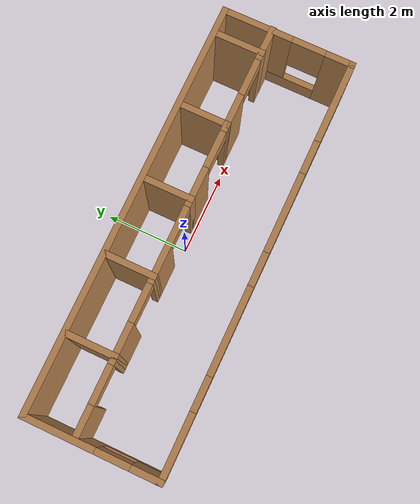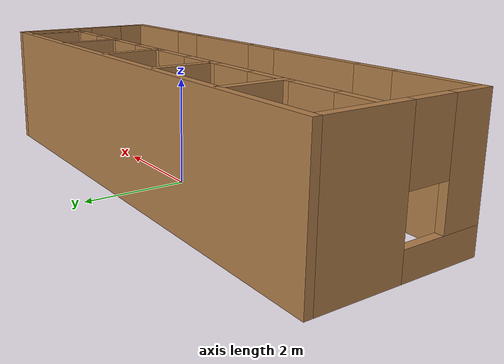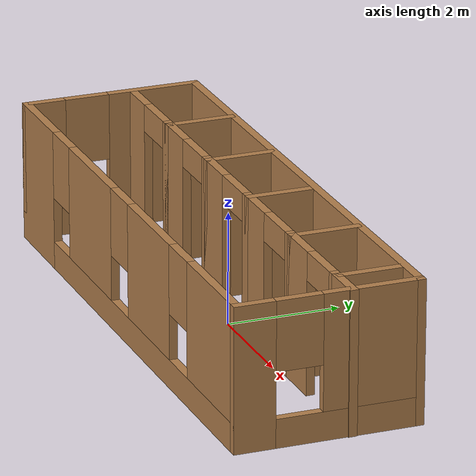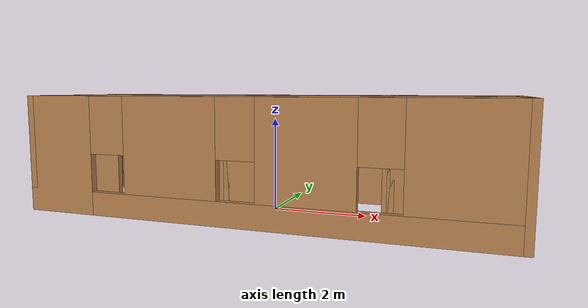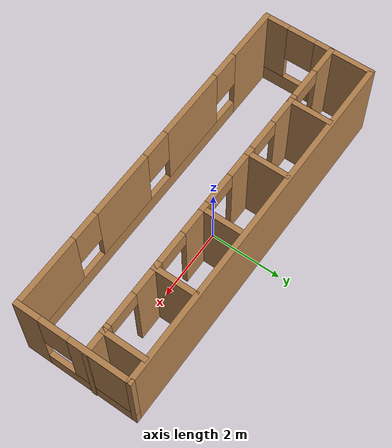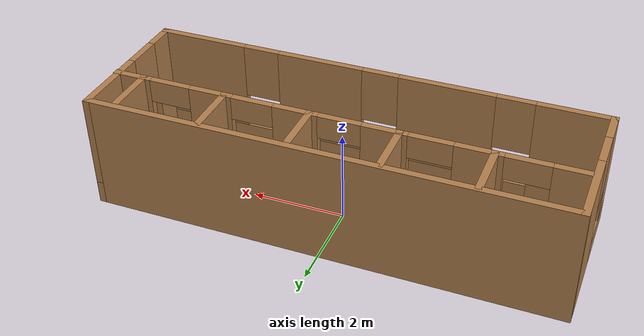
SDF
<?xml version='1.0'?>
<sdf version='1.7'>
  <model name='room'>
    <link name='Wall_10'>
      <pose>-2.14 0.1425 0 0 -0 0</pose>
      <self_collide>0</self_collide>
      <enable_wind>0</enable_wind>
      <kinematic>0</kinematic>
      <visual name='Wall_10_Visual_0'>
        <pose>-0.574862 0 1.25 0 -0 0</pose>
        <geometry>
          <box>
            <size>0.850276 0.15 2.5</size>
          </box>
        </geometry>
        <material>
          <script>
            <uri>file://media/materials/scripts/gazebo.material</uri>
            <name>Gazebo/Wood</name>
          </script>
          <ambient>1 1 1 1</ambient>
          <shader type='pixel'/>
        </material>
        <meta>
          <layer>0</layer>
        </meta>
        <transparency>0</transparency>
        <cast_shadows>1</cast_shadows>
      </visual>
      <visual name='Wall_10_Visual_1'>
        <pose>0.875138 0 1.25 0 -0 0</pose>
        <geometry>
          <box>
            <size>0.249724 0.15 2.5</size>
          </box>
        </geometry>
        <material>
          <script>
            <uri>file://media/materials/scripts/gazebo.material</uri>
            <name>Gazebo/Wood</name>
          </script>
          <ambient>1 1 1 1</ambient>
          <shader type='pixel'/>
        </material>
        <meta>
          <layer>0</layer>
        </meta>
        <transparency>0</transparency>
        <cast_shadows>1</cast_shadows>
      </visual>
      <visual name='Wall_10_Visual_2'>
        <pose>0.300276 0 2.25 0 -0 0</pose>
        <geometry>
          <box>
            <size>0.9 0.15 0.5</size>
          </box>
        </geometry>
        <material>
          <script>
            <uri>file://media/materials/scripts/gazebo.material</uri>
            <name>Gazebo/Wood</name>
          </script>
          <ambient>1 1 1 1</ambient>
          <shader type='pixel'/>
        </material>
        <meta>
          <layer>0</layer>
        </meta>
        <transparency>0</transparency>
        <cast_shadows>1</cast_shadows>
      </visual>
      <collision name='Wall_10_Collision_0'>
        <laser_retro>0</laser_retro>
        <max_contacts>10</max_contacts>
        <pose>-0.574862 0 1.25 0 -0 0</pose>
        <geometry>
          <box>
            <size>0.850276 0.15 2.5</size>
          </box>
        </geometry>
        <surface>
          <friction>
            <ode>
              <mu>1</mu>
              <mu2>1</mu2>
              <fdir1>0 0 0</fdir1>
              <slip1>0</slip1>
              <slip2>0</slip2>
            </ode>
            <torsional>
              <coefficient>1</coefficient>
              <patch_radius>0</patch_radius>
              <surface_radius>0</surface_radius>
              <use_patch_radius>1</use_patch_radius>
              <ode>
                <slip>0</slip>
              </ode>
            </torsional>
          </friction>
          <bounce>
            <restitution_coefficient>0</restitution_coefficient>
            <threshold>1e+06</threshold>
          </bounce>
          <contact>
            <collide_without_contact>0</collide_without_contact>
            <collide_without_contact_bitmask>1</collide_without_contact_bitmask>
            <collide_bitmask>1</collide_bitmask>
            <ode>
              <soft_cfm>0</soft_cfm>
              <soft_erp>0.2</soft_erp>
              <kp>1e+13</kp>
              <kd>1</kd>
              <max_vel>0.01</max_vel>
              <min_depth>0</min_depth>
            </ode>
            <bullet>
              <split_impulse>1</split_impulse>
              <split_impulse_penetration_threshold>-0.01</split_impulse_penetration_threshold>
              <soft_cfm>0</soft_cfm>
              <soft_erp>0.2</soft_erp>
              <kp>1e+13</kp>
              <kd>1</kd>
            </bullet>
          </contact>
        </surface>
      </collision>
      <collision name='Wall_10_Collision_1'>
        <laser_retro>0</laser_retro>
        <max_contacts>10</max_contacts>
        <pose>0.875138 0 1.25 0 -0 0</pose>
        <geometry>
          <box>
            <size>0.249724 0.15 2.5</size>
          </box>
        </geometry>
        <surface>
          <friction>
            <ode>
              <mu>1</mu>
              <mu2>1</mu2>
              <fdir1>0 0 0</fdir1>
              <slip1>0</slip1>
              <slip2>0</slip2>
            </ode>
            <torsional>
              <coefficient>1</coefficient>
              <patch_radius>0</patch_radius>
              <surface_radius>0</surface_radius>
              <use_patch_radius>1</use_patch_radius>
              <ode>
                <slip>0</slip>
              </ode>
            </torsional>
          </friction>
          <bounce>
            <restitution_coefficient>0</restitution_coefficient>
            <threshold>1e+06</threshold>
          </bounce>
          <contact>
            <collide_without_contact>0</collide_without_contact>
            <collide_without_contact_bitmask>1</collide_without_contact_bitmask>
            <collide_bitmask>1</collide_bitmask>
            <ode>
              <soft_cfm>0</soft_cfm>
              <soft_erp>0.2</soft_erp>
              <kp>1e+13</kp>
              <kd>1</kd>
              <max_vel>0.01</max_vel>
              <min_depth>0</min_depth>
            </ode>
            <bullet>
              <split_impulse>1</split_impulse>
              <split_impulse_penetration_threshold>-0.01</split_impulse_penetration_threshold>
              <soft_cfm>0</soft_cfm>
              <soft_erp>0.2</soft_erp>
              <kp>1e+13</kp>
              <kd>1</kd>
            </bullet>
          </contact>
        </surface>
      </collision>
      <collision name='Wall_10_Collision_2'>
        <laser_retro>0</laser_retro>
        <max_contacts>10</max_contacts>
        <pose>0.300276 0 2.25 0 -0 0</pose>
        <geometry>
          <box>
            <size>0.9 0.15 0.5</size>
          </box>
        </geometry>
        <surface>
          <friction>
            <ode>
              <mu>1</mu>
              <mu2>1</mu2>
              <fdir1>0 0 0</fdir1>
              <slip1>0</slip1>
              <slip2>0</slip2>
            </ode>
            <torsional>
              <coefficient>1</coefficient>
              <patch_radius>0</patch_radius>
              <surface_radius>0</surface_radius>
              <use_patch_radius>1</use_patch_radius>
              <ode>
                <slip>0</slip>
              </ode>
            </torsional>
          </friction>
          <bounce>
            <restitution_coefficient>0</restitution_coefficient>
            <threshold>1e+06</threshold>
          </bounce>
          <contact>
            <collide_without_contact>0</collide_without_contact>
            <collide_without_contact_bitmask>1</collide_without_contact_bitmask>
            <collide_bitmask>1</collide_bitmask>
            <ode>
              <soft_cfm>0</soft_cfm>
              <soft_erp>0.2</soft_erp>
              <kp>1e+13</kp>
              <kd>1</kd>
              <max_vel>0.01</max_vel>
              <min_depth>0</min_depth>
            </ode>
            <bullet>
              <split_impulse>1</split_impulse>
              <split_impulse_penetration_threshold>-0.01</split_impulse_penetration_threshold>
              <soft_cfm>0</soft_cfm>
              <soft_erp>0.2</soft_erp>
              <kp>1e+13</kp>
              <kd>1</kd>
            </bullet>
          </contact>
        </surface>
      </collision>
    </link>
    <link name='Wall_11'>
      <pose>-1.215 0.6925 0 0 -0 1.5708</pose>
      <self_collide>0</self_collide>
      <enable_wind>0</enable_wind>
      <kinematic>0</kinematic>
      <visual name='Wall_11_Visual'>
        <pose>0 0 1.25 0 -0 0</pose>
        <geometry>
          <box>
            <size>1.25 0.15 2.5</size>
          </box>
        </geometry>
        <material>
          <script>
            <uri>file://media/materials/scripts/gazebo.material</uri>
            <name>Gazebo/Wood</name>
          </script>
          <ambient>1 1 1 1</ambient>
          <shader type='pixel'/>
        </material>
        <meta>
          <layer>0</layer>
        </meta>
        <transparency>0</transparency>
        <cast_shadows>1</cast_shadows>
      </visual>
      <collision name='Wall_11_Collision'>
        <laser_retro>0</laser_retro>
        <max_contacts>10</max_contacts>
        <pose>0 0 1.25 0 -0 0</pose>
        <geometry>
          <box>
            <size>1.25 0.15 2.5</size>
          </box>
        </geometry>
        <surface>
          <friction>
            <ode>
              <mu>1</mu>
              <mu2>1</mu2>
              <fdir1>0 0 0</fdir1>
              <slip1>0</slip1>
              <slip2>0</slip2>
            </ode>
            <torsional>
              <coefficient>1</coefficient>
              <patch_radius>0</patch_radius>
              <surface_radius>0</surface_radius>
              <use_patch_radius>1</use_patch_radius>
              <ode>
                <slip>0</slip>
              </ode>
            </torsional>
          </friction>
          <bounce>
            <restitution_coefficient>0</restitution_coefficient>
            <threshold>1e+06</threshold>
          </bounce>
          <contact>
            <collide_without_contact>0</collide_without_contact>
            <collide_without_contact_bitmask>1</collide_without_contact_bitmask>
            <collide_bitmask>1</collide_bitmask>
            <ode>
              <soft_cfm>0</soft_cfm>
              <soft_erp>0.2</soft_erp>
              <kp>1e+13</kp>
              <kd>1</kd>
              <max_vel>0.01</max_vel>
              <min_depth>0</min_depth>
            </ode>
            <bullet>
              <split_impulse>1</split_impulse>
              <split_impulse_penetration_threshold>-0.01</split_impulse_penetration_threshold>
              <soft_cfm>0</soft_cfm>
              <soft_erp>0.2</soft_erp>
              <kp>1e+13</kp>
              <kd>1</kd>
            </bullet>
          </contact>
        </surface>
      </collision>
    </link>
    <link name='Wall_13'>
      <pose>-0.29 0.1425 0 0 -0 0</pose>
      <self_collide>0</self_collide>
      <enable_wind>0</enable_wind>
      <kinematic>0</kinematic>
      <visual name='Wall_13_Visual_0'>
        <pose>-0.579862 0 1.25 0 -0 0</pose>
        <geometry>
          <box>
            <size>0.840276 0.15 2.5</size>
          </box>
        </geometry>
        <material>
          <script>
            <uri>file://media/materials/scripts/gazebo.material</uri>
            <name>Gazebo/Wood</name>
          </script>
          <ambient>1 1 1 1</ambient>
          <shader type='pixel'/>
        </material>
        <meta>
          <layer>0</layer>
        </meta>
        <transparency>0</transparency>
        <cast_shadows>1</cast_shadows>
      </visual>
      <visual name='Wall_13_Visual_1'>
        <pose>0.870138 0 1.25 0 -0 0</pose>
        <geometry>
          <box>
            <size>0.259724 0.15 2.5</size>
          </box>
        </geometry>
        <material>
          <script>
            <uri>file://media/materials/scripts/gazebo.material</uri>
            <name>Gazebo/Wood</name>
          </script>
          <ambient>1 1 1 1</ambient>
          <shader type='pixel'/>
        </material>
        <meta>
          <layer>0</layer>
        </meta>
        <transparency>0</transparency>
        <cast_shadows>1</cast_shadows>
      </visual>
      <visual name='Wall_13_Visual_2'>
        <pose>0.290276 0 2.25 0 -0 0</pose>
        <geometry>
          <box>
            <size>0.9 0.15 0.5</size>
          </box>
        </geometry>
        <material>
          <script>
            <uri>file://media/materials/scripts/gazebo.material</uri>
            <name>Gazebo/Wood</name>
          </script>
          <ambient>1 1 1 1</ambient>
          <shader type='pixel'/>
        </material>
        <meta>
          <layer>0</layer>
        </meta>
        <transparency>0</transparency>
        <cast_shadows>1</cast_shadows>
      </visual>
      <collision name='Wall_13_Collision_0'>
        <laser_retro>0</laser_retro>
        <max_contacts>10</max_contacts>
        <pose>-0.579862 0 1.25 0 -0 0</pose>
        <geometry>
          <box>
            <size>0.840276 0.15 2.5</size>
          </box>
        </geometry>
        <surface>
          <friction>
            <ode>
              <mu>1</mu>
              <mu2>1</mu2>
              <fdir1>0 0 0</fdir1>
              <slip1>0</slip1>
              <slip2>0</slip2>
            </ode>
            <torsional>
              <coefficient>1</coefficient>
              <patch_radius>0</patch_radius>
              <surface_radius>0</surface_radius>
              <use_patch_radius>1</use_patch_radius>
              <ode>
                <slip>0</slip>
              </ode>
            </torsional>
          </friction>
          <bounce>
            <restitution_coefficient>0</restitution_coefficient>
            <threshold>1e+06</threshold>
          </bounce>
          <contact>
            <collide_without_contact>0</collide_without_contact>
            <collide_without_contact_bitmask>1</collide_without_contact_bitmask>
            <collide_bitmask>1</collide_bitmask>
            <ode>
              <soft_cfm>0</soft_cfm>
              <soft_erp>0.2</soft_erp>
              <kp>1e+13</kp>
              <kd>1</kd>
              <max_vel>0.01</max_vel>
              <min_depth>0</min_depth>
            </ode>
            <bullet>
              <split_impulse>1</split_impulse>
              <split_impulse_penetration_threshold>-0.01</split_impulse_penetration_threshold>
              <soft_cfm>0</soft_cfm>
              <soft_erp>0.2</soft_erp>
              <kp>1e+13</kp>
              <kd>1</kd>
            </bullet>
          </contact>
        </surface>
      </collision>
      <collision name='Wall_13_Collision_2'>
        <laser_retro>0</laser_retro>
        <max_contacts>10</max_contacts>
        <pose>0.290276 0 2.25 0 -0 0</pose>
        <geometry>
          <box>
            <size>0.9 0.15 0.5</size>
          </box>
        </geometry>
        <surface>
          <friction>
            <ode>
              <mu>1</mu>
              <mu2>1</mu2>
              <fdir1>0 0 0</fdir1>
              <slip1>0</slip1>
              <slip2>0</slip2>
            </ode>
            <torsional>
              <coefficient>1</coefficient>
              <patch_radius>0</patch_radius>
              <surface_radius>0</surface_radius>
              <use_patch_radius>1</use_patch_radius>
              <ode>
                <slip>0</slip>
              </ode>
            </torsional>
          </friction>
          <bounce>
            <restitution_coefficient>0</restitution_coefficient>
            <threshold>1e+06</threshold>
          </bounce>
          <contact>
            <collide_without_contact>0</collide_without_contact>
            <collide_without_contact_bitmask>1</collide_without_contact_bitmask>
            <collide_bitmask>1</collide_bitmask>
            <ode>
              <soft_cfm>0</soft_cfm>
              <soft_erp>0.2</soft_erp>
              <kp>1e+13</kp>
              <kd>1</kd>
              <max_vel>0.01</max_vel>
              <min_depth>0</min_depth>
            </ode>
            <bullet>
              <split_impulse>1</split_impulse>
              <split_impulse_penetration_threshold>-0.01</split_impulse_penetration_threshold>
              <soft_cfm>0</soft_cfm>
              <soft_erp>0.2</soft_erp>
              <kp>1e+13</kp>
              <kd>1</kd>
            </bullet>
          </contact>
        </surface>
      </collision>
      <collision name='Wall_13_Collision_1'>
        <laser_retro>0</laser_retro>
        <max_contacts>10</max_contacts>
        <pose>0.870138 0 1.25 0 -0 0</pose>
        <geometry>
          <box>
            <size>0.259724 0.15 2.5</size>
          </box>
        </geometry>
        <surface>
          <friction>
            <ode>
              <mu>1</mu>
              <mu2>1</mu2>
              <fdir1>0 0 0</fdir1>
              <slip1>0</slip1>
              <slip2>0</slip2>
            </ode>
            <torsional>
              <coefficient>1</coefficient>
              <patch_radius>0</patch_radius>
              <surface_radius>0</surface_radius>
              <use_patch_radius>1</use_patch_radius>
              <ode>
                <slip>0</slip>
              </ode>
            </torsional>
          </friction>
          <bounce>
            <restitution_coefficient>0</restitution_coefficient>
            <threshold>1e+06</threshold>
          </bounce>
          <contact>
            <collide_without_contact>0</collide_without_contact>
            <collide_without_contact_bitmask>1</collide_without_contact_bitmask>
            <collide_bitmask>1</collide_bitmask>
            <ode>
              <soft_cfm>0</soft_cfm>
              <soft_erp>0.2</soft_erp>
              <kp>1e+13</kp>
              <kd>1</kd>
              <max_vel>0.01</max_vel>
              <min_depth>0</min_depth>
            </ode>
            <bullet>
              <split_impulse>1</split_impulse>
              <split_impulse_penetration_threshold>-0.01</split_impulse_penetration_threshold>
              <soft_cfm>0</soft_cfm>
              <soft_erp>0.2</soft_erp>
              <kp>1e+13</kp>
              <kd>1</kd>
            </bullet>
          </contact>
        </surface>
      </collision>
    </link>
    <link name='Wall_14'>
      <pose>0.635 0.6925 0 0 -0 1.5708</pose>
      <self_collide>0</self_collide>
      <enable_wind>0</enable_wind>
      <kinematic>0</kinematic>
      <visual name='Wall_14_Visual'>
        <pose>0 0 1.25 0 -0 0</pose>
        <geometry>
          <box>
            <size>1.25 0.15 2.5</size>
          </box>
        </geometry>
        <material>
          <script>
            <uri>file://media/materials/scripts/gazebo.material</uri>
            <name>Gazebo/Wood</name>
          </script>
          <ambient>1 1 1 1</ambient>
          <shader type='pixel'/>
        </material>
        <meta>
          <layer>0</layer>
        </meta>
        <transparency>0</transparency>
        <cast_shadows>1</cast_shadows>
      </visual>
      <collision name='Wall_14_Collision'>
        <laser_retro>0</laser_retro>
        <max_contacts>10</max_contacts>
        <pose>0 0 1.25 0 -0 0</pose>
        <geometry>
          <box>
            <size>1.25 0.15 2.5</size>
          </box>
        </geometry>
        <surface>
          <friction>
            <ode>
              <mu>1</mu>
              <mu2>1</mu2>
              <fdir1>0 0 0</fdir1>
              <slip1>0</slip1>
              <slip2>0</slip2>
            </ode>
            <torsional>
              <coefficient>1</coefficient>
              <patch_radius>0</patch_radius>
              <surface_radius>0</surface_radius>
              <use_patch_radius>1</use_patch_radius>
              <ode>
                <slip>0</slip>
              </ode>
            </torsional>
          </friction>
          <bounce>
            <restitution_coefficient>0</restitution_coefficient>
            <threshold>1e+06</threshold>
          </bounce>
          <contact>
            <collide_without_contact>0</collide_without_contact>
            <collide_without_contact_bitmask>1</collide_without_contact_bitmask>
            <collide_bitmask>1</collide_bitmask>
            <ode>
              <soft_cfm>0</soft_cfm>
              <soft_erp>0.2</soft_erp>
              <kp>1e+13</kp>
              <kd>1</kd>
              <max_vel>0.01</max_vel>
              <min_depth>0</min_depth>
            </ode>
            <bullet>
              <split_impulse>1</split_impulse>
              <split_impulse_penetration_threshold>-0.01</split_impulse_penetration_threshold>
              <soft_cfm>0</soft_cfm>
              <soft_erp>0.2</soft_erp>
              <kp>1e+13</kp>
              <kd>1</kd>
            </bullet>
          </contact>
        </surface>
      </collision>
    </link>
    <link name='Wall_2'>
      <pose>-0.01 -1.7975 0 0 -0 0</pose>
      <self_collide>0</self_collide>
      <enable_wind>0</enable_wind>
      <kinematic>0</kinematic>
      <visual name='Wall_2_Visual_0'>
        <pose>-4.19986 0 1.25 0 -0 0</pose>
        <geometry>
          <box>
            <size>1.60028 0.15 2.5</size>
          </box>
        </geometry>
        <material>
          <script>
            <uri>file://media/materials/scripts/gazebo.material</uri>
            <name>Gazebo/Wood</name>
          </script>
          <ambient>1 1 1 1</ambient>
          <shader type='pixel'/>
        </material>
        <meta>
          <layer>0</layer>
        </meta>
        <transparency>0</transparency>
        <cast_shadows>1</cast_shadows>
      </visual>
      <visual name='Wall_2_Visual_1'>
        <pose>0.800138 0 0.25 0 -0 0</pose>
        <geometry>
          <box>
            <size>8.39972 0.15 0.5</size>
          </box>
        </geometry>
        <material>
          <script>
            <uri>file://media/materials/scripts/gazebo.material</uri>
            <name>Gazebo/Wood</name>
          </script>
          <ambient>1 1 1 1</ambient>
          <shader type='pixel'/>
        </material>
        <meta>
          <layer>0</layer>
        </meta>
        <transparency>0</transparency>
        <cast_shadows>1</cast_shadows>
      </visual>
      <visual name='Wall_2_Visual_2'>
        <pose>-1.56972 0 1.5 0 -0 0</pose>
        <geometry>
          <box>
            <size>2.06 0.15 2</size>
          </box>
        </geometry>
        <material>
          <script>
            <uri>file://media/materials/scripts/gazebo.material</uri>
            <name>Gazebo/Wood</name>
          </script>
          <ambient>1 1 1 1</ambient>
          <shader type='pixel'/>
        </material>
        <meta>
          <layer>0</layer>
        </meta>
        <transparency>0</transparency>
        <cast_shadows>1</cast_shadows>
      </visual>
      <visual name='Wall_2_Visual_3'>
        <pose>1.21528 0 1.5 0 -0 0</pose>
        <geometry>
          <box>
            <size>1.91 0.15 2</size>
          </box>
        </geometry>
        <material>
          <script>
            <uri>file://media/materials/scripts/gazebo.material</uri>
            <name>Gazebo/Wood</name>
          </script>
          <ambient>1 1 1 1</ambient>
          <shader type='pixel'/>
        </material>
        <meta>
          <layer>0</layer>
        </meta>
        <transparency>0</transparency>
        <cast_shadows>1</cast_shadows>
      </visual>
      <visual name='Wall_2_Visual_4'>
        <pose>3.98514 0 1.5 0 -0 0</pose>
        <geometry>
          <box>
            <size>2.02972 0.15 2</size>
          </box>
        </geometry>
        <material>
          <script>
            <uri>file://media/materials/scripts/gazebo.material</uri>
            <name>Gazebo/Wood</name>
          </script>
          <ambient>1 1 1 1</ambient>
          <shader type='pixel'/>
        </material>
        <meta>
          <layer>0</layer>
        </meta>
        <transparency>0</transparency>
        <cast_shadows>1</cast_shadows>
      </visual>
      <visual name='Wall_2_Visual_5'>
        <pose>-2.99972 0 1.9 0 -0 0</pose>
        <geometry>
          <box>
            <size>0.8 0.15 1.2</size>
          </box>
        </geometry>
        <material>
          <script>
            <uri>file://media/materials/scripts/gazebo.material</uri>
            <name>Gazebo/Wood</name>
          </script>
          <ambient>1 1 1 1</ambient>
          <shader type='pixel'/>
        </material>
        <meta>
          <layer>0</layer>
        </meta>
        <transparency>0</transparency>
        <cast_shadows>1</cast_shadows>
      </visual>
      <visual name='Wall_2_Visual_6'>
        <pose>-0.139724 0 1.9 0 -0 0</pose>
        <geometry>
          <box>
            <size>0.8 0.15 1.2</size>
          </box>
        </geometry>
        <material>
          <script>
            <uri>file://media/materials/scripts/gazebo.material</uri>
            <name>Gazebo/Wood</name>
          </script>
          <ambient>1 1 1 1</ambient>
          <shader type='pixel'/>
        </material>
        <meta>
          <layer>0</layer>
        </meta>
        <transparency>0</transparency>
        <cast_shadows>1</cast_shadows>
      </visual>
      <visual name='Wall_2_Visual_7'>
        <pose>2.57028 0 1.9 0 -0 0</pose>
        <geometry>
          <box>
            <size>0.8 0.15 1.2</size>
          </box>
        </geometry>
        <material>
          <script>
            <uri>file://media/materials/scripts/gazebo.material</uri>
            <name>Gazebo/Wood</name>
          </script>
          <ambient>1 1 1 1</ambient>
          <shader type='pixel'/>
        </material>
        <meta>
          <layer>0</layer>
        </meta>
        <transparency>0</transparency>
        <cast_shadows>1</cast_shadows>
      </visual>
      <collision name='Wall_2_Collision_0'>
        <laser_retro>0</laser_retro>
        <max_contacts>10</max_contacts>
        <pose>-4.19986 0 1.25 0 -0 0</pose>
        <geometry>
          <box>
            <size>1.60028 0.15 2.5</size>
          </box>
        </geometry>
        <surface>
          <friction>
            <ode>
              <mu>1</mu>
              <mu2>1</mu2>
              <fdir1>0 0 0</fdir1>
              <slip1>0</slip1>
              <slip2>0</slip2>
            </ode>
            <torsional>
              <coefficient>1</coefficient>
              <patch_radius>0</patch_radius>
              <surface_radius>0</surface_radius>
              <use_patch_radius>1</use_patch_radius>
              <ode>
                <slip>0</slip>
              </ode>
            </torsional>
          </friction>
          <bounce>
            <restitution_coefficient>0</restitution_coefficient>
            <threshold>1e+06</threshold>
          </bounce>
          <contact>
            <collide_without_contact>0</collide_without_contact>
            <collide_without_contact_bitmask>1</collide_without_contact_bitmask>
            <collide_bitmask>1</collide_bitmask>
            <ode>
              <soft_cfm>0</soft_cfm>
              <soft_erp>0.2</soft_erp>
              <kp>1e+13</kp>
              <kd>1</kd>
              <max_vel>0.01</max_vel>
              <min_depth>0</min_depth>
            </ode>
            <bullet>
              <split_impulse>1</split_impulse>
              <split_impulse_penetration_threshold>-0.01</split_impulse_penetration_threshold>
              <soft_cfm>0</soft_cfm>
              <soft_erp>0.2</soft_erp>
              <kp>1e+13</kp>
              <kd>1</kd>
            </bullet>
          </contact>
        </surface>
      </collision>
      <collision name='Wall_2_Collision_1'>
        <laser_retro>0</laser_retro>
        <max_contacts>10</max_contacts>
        <pose>0.800138 0 0.25 0 -0 0</pose>
        <geometry>
          <box>
            <size>8.39972 0.15 0.5</size>
          </box>
        </geometry>
        <surface>
          <friction>
            <ode>
              <mu>1</mu>
              <mu2>1</mu2>
              <fdir1>0 0 0</fdir1>
              <slip1>0</slip1>
              <slip2>0</slip2>
            </ode>
            <torsional>
              <coefficient>1</coefficient>
              <patch_radius>0</patch_radius>
              <surface_radius>0</surface_radius>
              <use_patch_radius>1</use_patch_radius>
              <ode>
                <slip>0</slip>
              </ode>
            </torsional>
          </friction>
          <bounce>
            <restitution_coefficient>0</restitution_coefficient>
            <threshold>1e+06</threshold>
          </bounce>
          <contact>
            <collide_without_contact>0</collide_without_contact>
            <collide_without_contact_bitmask>1</collide_without_contact_bitmask>
            <collide_bitmask>1</collide_bitmask>
            <ode>
              <soft_cfm>0</soft_cfm>
              <soft_erp>0.2</soft_erp>
              <kp>1e+13</kp>
              <kd>1</kd>
              <max_vel>0.01</max_vel>
              <min_depth>0</min_depth>
            </ode>
            <bullet>
              <split_impulse>1</split_impulse>
              <split_impulse_penetration_threshold>-0.01</split_impulse_penetration_threshold>
              <soft_cfm>0</soft_cfm>
              <soft_erp>0.2</soft_erp>
              <kp>1e+13</kp>
              <kd>1</kd>
            </bullet>
          </contact>
        </surface>
      </collision>
      <collision name='Wall_2_Collision_2'>
        <laser_retro>0</laser_retro>
        <max_contacts>10</max_contacts>
        <pose>-1.56972 0 1.5 0 -0 0</pose>
        <geometry>
          <box>
            <size>2.06 0.15 2</size>
          </box>
        </geometry>
        <surface>
          <friction>
            <ode>
              <mu>1</mu>
              <mu2>1</mu2>
              <fdir1>0 0 0</fdir1>
              <slip1>0</slip1>
              <slip2>0</slip2>
            </ode>
            <torsional>
              <coefficient>1</coefficient>
              <patch_radius>0</patch_radius>
              <surface_radius>0</surface_radius>
              <use_patch_radius>1</use_patch_radius>
              <ode>
                <slip>0</slip>
              </ode>
            </torsional>
          </friction>
          <bounce>
            <restitution_coefficient>0</restitution_coefficient>
            <threshold>1e+06</threshold>
          </bounce>
          <contact>
            <collide_without_contact>0</collide_without_contact>
            <collide_without_contact_bitmask>1</collide_without_contact_bitmask>
            <collide_bitmask>1</collide_bitmask>
            <ode>
              <soft_cfm>0</soft_cfm>
              <soft_erp>0.2</soft_erp>
              <kp>1e+13</kp>
              <kd>1</kd>
              <max_vel>0.01</max_vel>
              <min_depth>0</min_depth>
            </ode>
            <bullet>
              <split_impulse>1</split_impulse>
              <split_impulse_penetration_threshold>-0.01</split_impulse_penetration_threshold>
              <soft_cfm>0</soft_cfm>
              <soft_erp>0.2</soft_erp>
              <kp>1e+13</kp>
              <kd>1</kd>
            </bullet>
          </contact>
        </surface>
      </collision>
      <collision name='Wall_2_Collision_4'>
        <laser_retro>0</laser_retro>
        <max_contacts>10</max_contacts>
        <pose>3.98514 0 1.5 0 -0 0</pose>
        <geometry>
          <box>
            <size>2.02972 0.15 2</size>
          </box>
        </geometry>
        <surface>
          <friction>
            <ode>
              <mu>1</mu>
              <mu2>1</mu2>
              <fdir1>0 0 0</fdir1>
              <slip1>0</slip1>
              <slip2>0</slip2>
            </ode>
            <torsional>
              <coefficient>1</coefficient>
              <patch_radius>0</patch_radius>
              <surface_radius>0</surface_radius>
              <use_patch_radius>1</use_patch_radius>
              <ode>
                <slip>0</slip>
              </ode>
            </torsional>
          </friction>
          <bounce>
            <restitution_coefficient>0</restitution_coefficient>
            <threshold>1e+06</threshold>
          </bounce>
          <contact>
            <collide_without_contact>0</collide_without_contact>
            <collide_without_contact_bitmask>1</collide_without_contact_bitmask>
            <collide_bitmask>1</collide_bitmask>
            <ode>
              <soft_cfm>0</soft_cfm>
              <soft_erp>0.2</soft_erp>
              <kp>1e+13</kp>
              <kd>1</kd>
              <max_vel>0.01</max_vel>
              <min_depth>0</min_depth>
            </ode>
            <bullet>
              <split_impulse>1</split_impulse>
              <split_impulse_penetration_threshold>-0.01</split_impulse_penetration_threshold>
              <soft_cfm>0</soft_cfm>
              <soft_erp>0.2</soft_erp>
              <kp>1e+13</kp>
              <kd>1</kd>
            </bullet>
          </contact>
        </surface>
      </collision>
      <collision name='Wall_2_Collision_3'>
        <laser_retro>0</laser_retro>
        <max_contacts>10</max_contacts>
        <pose>1.21528 0 1.5 0 -0 0</pose>
        <geometry>
          <box>
            <size>1.91 0.15 2</size>
          </box>
        </geometry>
        <surface>
          <friction>
            <ode>
              <mu>1</mu>
              <mu2>1</mu2>
              <fdir1>0 0 0</fdir1>
              <slip1>0</slip1>
              <slip2>0</slip2>
            </ode>
            <torsional>
              <coefficient>1</coefficient>
              <patch_radius>0</patch_radius>
              <surface_radius>0</surface_radius>
              <use_patch_radius>1</use_patch_radius>
              <ode>
                <slip>0</slip>
              </ode>
            </torsional>
          </friction>
          <bounce>
            <restitution_coefficient>0</restitution_coefficient>
            <threshold>1e+06</threshold>
          </bounce>
          <contact>
            <collide_without_contact>0</collide_without_contact>
            <collide_without_contact_bitmask>1</collide_without_contact_bitmask>
            <collide_bitmask>1</collide_bitmask>
            <ode>
              <soft_cfm>0</soft_cfm>
              <soft_erp>0.2</soft_erp>
              <kp>1e+13</kp>
              <kd>1</kd>
              <max_vel>0.01</max_vel>
              <min_depth>0</min_depth>
            </ode>
            <bullet>
              <split_impulse>1</split_impulse>
              <split_impulse_penetration_threshold>-0.01</split_impulse_penetration_threshold>
              <soft_cfm>0</soft_cfm>
              <soft_erp>0.2</soft_erp>
              <kp>1e+13</kp>
              <kd>1</kd>
            </bullet>
          </contact>
        </surface>
      </collision>
      <collision name='Wall_2_Collision_5'>
        <laser_retro>0</laser_retro>
        <max_contacts>10</max_contacts>
        <pose>-2.99972 0 1.9 0 -0 0</pose>
        <geometry>
          <box>
            <size>0.8 0.15 1.2</size>
          </box>
        </geometry>
        <surface>
          <friction>
            <ode>
              <mu>1</mu>
              <mu2>1</mu2>
              <fdir1>0 0 0</fdir1>
              <slip1>0</slip1>
              <slip2>0</slip2>
            </ode>
            <torsional>
              <coefficient>1</coefficient>
              <patch_radius>0</patch_radius>
              <surface_radius>0</surface_radius>
              <use_patch_radius>1</use_patch_radius>
              <ode>
                <slip>0</slip>
              </ode>
            </torsional>
          </friction>
          <bounce>
            <restitution_coefficient>0</restitution_coefficient>
            <threshold>1e+06</threshold>
          </bounce>
          <contact>
            <collide_without_contact>0</collide_without_contact>
            <collide_without_contact_bitmask>1</collide_without_contact_bitmask>
            <collide_bitmask>1</collide_bitmask>
            <ode>
              <soft_cfm>0</soft_cfm>
              <soft_erp>0.2</soft_erp>
              <kp>1e+13</kp>
              <kd>1</kd>
              <max_vel>0.01</max_vel>
              <min_depth>0</min_depth>
            </ode>
            <bullet>
              <split_impulse>1</split_impulse>
              <split_impulse_penetration_threshold>-0.01</split_impulse_penetration_threshold>
              <soft_cfm>0</soft_cfm>
              <soft_erp>0.2</soft_erp>
              <kp>1e+13</kp>
              <kd>1</kd>
            </bullet>
          </contact>
        </surface>
      </collision>
      <collision name='Wall_2_Collision_6'>
        <laser_retro>0</laser_retro>
        <max_contacts>10</max_contacts>
        <pose>-0.139724 0 1.9 0 -0 0</pose>
        <geometry>
          <box>
            <size>0.8 0.15 1.2</size>
          </box>
        </geometry>
        <surface>
          <friction>
            <ode>
              <mu>1</mu>
              <mu2>1</mu2>
              <fdir1>0 0 0</fdir1>
              <slip1>0</slip1>
              <slip2>0</slip2>
            </ode>
            <torsional>
              <coefficient>1</coefficient>
              <patch_radius>0</patch_radius>
              <surface_radius>0</surface_radius>
              <use_patch_radius>1</use_patch_radius>
              <ode>
                <slip>0</slip>
              </ode>
            </torsional>
          </friction>
          <bounce>
            <restitution_coefficient>0</restitution_coefficient>
            <threshold>1e+06</threshold>
          </bounce>
          <contact>
            <collide_without_contact>0</collide_without_contact>
            <collide_without_contact_bitmask>1</collide_without_contact_bitmask>
            <collide_bitmask>1</collide_bitmask>
            <ode>
              <soft_cfm>0</soft_cfm>
              <soft_erp>0.2</soft_erp>
              <kp>1e+13</kp>
              <kd>1</kd>
              <max_vel>0.01</max_vel>
              <min_depth>0</min_depth>
            </ode>
            <bullet>
              <split_impulse>1</split_impulse>
              <split_impulse_penetration_threshold>-0.01</split_impulse_penetration_threshold>
              <soft_cfm>0</soft_cfm>
              <soft_erp>0.2</soft_erp>
              <kp>1e+13</kp>
              <kd>1</kd>
            </bullet>
          </contact>
        </surface>
      </collision>
      <collision name='Wall_2_Collision_7'>
        <laser_retro>0</laser_retro>
        <max_contacts>10</max_contacts>
        <pose>2.57028 0 1.9 0 -0 0</pose>
        <geometry>
          <box>
            <size>0.8 0.15 1.2</size>
          </box>
        </geometry>
        <surface>
          <friction>
            <ode>
              <mu>1</mu>
              <mu2>1</mu2>
              <fdir1>0 0 0</fdir1>
              <slip1>0</slip1>
              <slip2>0</slip2>
            </ode>
            <torsional>
              <coefficient>1</coefficient>
              <patch_radius>0</patch_radius>
              <surface_radius>0</surface_radius>
              <use_patch_radius>1</use_patch_radius>
              <ode>
                <slip>0</slip>
              </ode>
            </torsional>
          </friction>
          <bounce>
            <restitution_coefficient>0</restitution_coefficient>
            <threshold>1e+06</threshold>
          </bounce>
          <contact>
            <collide_without_contact>0</collide_without_contact>
            <collide_without_contact_bitmask>1</collide_without_contact_bitmask>
            <collide_bitmask>1</collide_bitmask>
            <ode>
              <soft_cfm>0</soft_cfm>
              <soft_erp>0.2</soft_erp>
              <kp>1e+13</kp>
              <kd>1</kd>
              <max_vel>0.01</max_vel>
              <min_depth>0</min_depth>
            </ode>
            <bullet>
              <split_impulse>1</split_impulse>
              <split_impulse_penetration_threshold>-0.01</split_impulse_penetration_threshold>
              <soft_cfm>0</soft_cfm>
              <soft_erp>0.2</soft_erp>
              <kp>1e+13</kp>
              <kd>1</kd>
            </bullet>
          </contact>
        </surface>
      </collision>
    </link>
    <link name='Wall_3'>
      <pose>4.915 -0.2475 0 0 -0 1.5708</pose>
      <self_collide>0</self_collide>
      <enable_wind>0</enable_wind>
      <kinematic>0</kinematic>
      <visual name='Wall_3_Visual_0'>
        <pose>-1.26897 0 1.25 0 -0 0</pose>
        <geometry>
          <box>
            <size>0.712063 0.15 2.5</size>
          </box>
        </geometry>
        <material>
          <script>
            <uri>file://media/materials/scripts/gazebo.material</uri>
            <name>Gazebo/Wood</name>
          </script>
          <ambient>1 1 1 1</ambient>
          <shader type='pixel'/>
        </material>
        <meta>
          <layer>0</layer>
        </meta>
        <transparency>0</transparency>
        <cast_shadows>1</cast_shadows>
      </visual>
      <visual name='Wall_3_Visual_1'>
        <pose>0.356032 0 0.25 0 -0 0</pose>
        <geometry>
          <box>
            <size>2.53794 0.15 0.5</size>
          </box>
        </geometry>
        <material>
          <script>
            <uri>file://media/materials/scripts/gazebo.material</uri>
            <name>Gazebo/Wood</name>
          </script>
          <ambient>1 1 1 1</ambient>
          <shader type='pixel'/>
        </material>
        <meta>
          <layer>0</layer>
        </meta>
        <transparency>0</transparency>
        <cast_shadows>1</cast_shadows>
      </visual>
      <visual name='Wall_3_Visual_3'>
        <pose>-0.512937 0 1.9 0 -0 0</pose>
        <geometry>
          <box>
            <size>0.8 0.15 1.2</size>
          </box>
        </geometry>
        <material>
          <script>
            <uri>file://media/materials/scripts/gazebo.material</uri>
            <name>Gazebo/Wood</name>
          </script>
          <ambient>1 1 1 1</ambient>
          <shader type='pixel'/>
        </material>
        <meta>
          <layer>0</layer>
        </meta>
        <transparency>0</transparency>
        <cast_shadows>1</cast_shadows>
      </visual>
      <visual name='Wall_3_Visual_2'>
        <pose>0.756032 0 1.5 0 -0 0</pose>
        <geometry>
          <box>
            <size>1.73794 0.15 2</size>
          </box>
        </geometry>
        <material>
          <script>
            <uri>file://media/materials/scripts/gazebo.material</uri>
            <name>Gazebo/Wood</name>
          </script>
          <ambient>1 1 1 1</ambient>
          <shader type='pixel'/>
        </material>
        <meta>
          <layer>0</layer>
        </meta>
        <transparency>0</transparency>
        <cast_shadows>1</cast_shadows>
      </visual>
      <collision name='Wall_3_Collision_0'>
        <laser_retro>0</laser_retro>
        <max_contacts>10</max_contacts>
        <pose>-1.26897 0 1.25 0 -0 0</pose>
        <geometry>
          <box>
            <size>0.712063 0.15 2.5</size>
          </box>
        </geometry>
        <surface>
          <friction>
            <ode>
              <mu>1</mu>
              <mu2>1</mu2>
              <fdir1>0 0 0</fdir1>
              <slip1>0</slip1>
              <slip2>0</slip2>
            </ode>
            <torsional>
              <coefficient>1</coefficient>
              <patch_radius>0</patch_radius>
              <surface_radius>0</surface_radius>
              <use_patch_radius>1</use_patch_radius>
              <ode>
                <slip>0</slip>
              </ode>
            </torsional>
          </friction>
          <bounce>
            <restitution_coefficient>0</restitution_coefficient>
            <threshold>1e+06</threshold>
          </bounce>
          <contact>
            <collide_without_contact>0</collide_without_contact>
            <collide_without_contact_bitmask>1</collide_without_contact_bitmask>
            <collide_bitmask>1</collide_bitmask>
            <ode>
              <soft_cfm>0</soft_cfm>
              <soft_erp>0.2</soft_erp>
              <kp>1e+13</kp>
              <kd>1</kd>
              <max_vel>0.01</max_vel>
              <min_depth>0</min_depth>
            </ode>
            <bullet>
              <split_impulse>1</split_impulse>
              <split_impulse_penetration_threshold>-0.01</split_impulse_penetration_threshold>
              <soft_cfm>0</soft_cfm>
              <soft_erp>0.2</soft_erp>
              <kp>1e+13</kp>
              <kd>1</kd>
            </bullet>
          </contact>
        </surface>
      </collision>
      <collision name='Wall_3_Collision_1'>
        <laser_retro>0</laser_retro>
        <max_contacts>10</max_contacts>
        <pose>0.356032 0 0.25 0 -0 0</pose>
        <geometry>
          <box>
            <size>2.53794 0.15 0.5</size>
          </box>
        </geometry>
        <surface>
          <friction>
            <ode>
              <mu>1</mu>
              <mu2>1</mu2>
              <fdir1>0 0 0</fdir1>
              <slip1>0</slip1>
              <slip2>0</slip2>
            </ode>
            <torsional>
              <coefficient>1</coefficient>
              <patch_radius>0</patch_radius>
              <surface_radius>0</surface_radius>
              <use_patch_radius>1</use_patch_radius>
              <ode>
                <slip>0</slip>
              </ode>
            </torsional>
          </friction>
          <bounce>
            <restitution_coefficient>0</restitution_coefficient>
            <threshold>1e+06</threshold>
          </bounce>
          <contact>
            <collide_without_contact>0</collide_without_contact>
            <collide_without_contact_bitmask>1</collide_without_contact_bitmask>
            <collide_bitmask>1</collide_bitmask>
            <ode>
              <soft_cfm>0</soft_cfm>
              <soft_erp>0.2</soft_erp>
              <kp>1e+13</kp>
              <kd>1</kd>
              <max_vel>0.01</max_vel>
              <min_depth>0</min_depth>
            </ode>
            <bullet>
              <split_impulse>1</split_impulse>
              <split_impulse_penetration_threshold>-0.01</split_impulse_penetration_threshold>
              <soft_cfm>0</soft_cfm>
              <soft_erp>0.2</soft_erp>
              <kp>1e+13</kp>
              <kd>1</kd>
            </bullet>
          </contact>
        </surface>
      </collision>
      <collision name='Wall_3_Collision_2'>
        <laser_retro>0</laser_retro>
        <max_contacts>10</max_contacts>
        <pose>0.756032 0 1.5 0 -0 0</pose>
        <geometry>
          <box>
            <size>1.73794 0.15 2</size>
          </box>
        </geometry>
        <surface>
          <friction>
            <ode>
              <mu>1</mu>
              <mu2>1</mu2>
              <fdir1>0 0 0</fdir1>
              <slip1>0</slip1>
              <slip2>0</slip2>
            </ode>
            <torsional>
              <coefficient>1</coefficient>
              <patch_radius>0</patch_radius>
              <surface_radius>0</surface_radius>
              <use_patch_radius>1</use_patch_radius>
              <ode>
                <slip>0</slip>
              </ode>
            </torsional>
          </friction>
          <bounce>
            <restitution_coefficient>0</restitution_coefficient>
            <threshold>1e+06</threshold>
          </bounce>
          <contact>
            <collide_without_contact>0</collide_without_contact>
            <collide_without_contact_bitmask>1</collide_without_contact_bitmask>
            <collide_bitmask>1</collide_bitmask>
            <ode>
              <soft_cfm>0</soft_cfm>
              <soft_erp>0.2</soft_erp>
              <kp>1e+13</kp>
              <kd>1</kd>
              <max_vel>0.01</max_vel>
              <min_depth>0</min_depth>
            </ode>
            <bullet>
              <split_impulse>1</split_impulse>
              <split_impulse_penetration_threshold>-0.01</split_impulse_penetration_threshold>
              <soft_cfm>0</soft_cfm>
              <soft_erp>0.2</soft_erp>
              <kp>1e+13</kp>
              <kd>1</kd>
            </bullet>
          </contact>
        </surface>
      </collision>
      <collision name='Wall_3_Collision_3'>
        <laser_retro>0</laser_retro>
        <max_contacts>10</max_contacts>
        <pose>-0.512937 0 1.9 0 -0 0</pose>
        <geometry>
          <box>
            <size>0.8 0.15 1.2</size>
          </box>
        </geometry>
        <surface>
          <friction>
            <ode>
              <mu>1</mu>
              <mu2>1</mu2>
              <fdir1>0 0 0</fdir1>
              <slip1>0</slip1>
              <slip2>0</slip2>
            </ode>
            <torsional>
              <coefficient>1</coefficient>
              <patch_radius>0</patch_radius>
              <surface_radius>0</surface_radius>
              <use_patch_radius>1</use_patch_radius>
              <ode>
                <slip>0</slip>
              </ode>
            </torsional>
          </friction>
          <bounce>
            <restitution_coefficient>0</restitution_coefficient>
            <threshold>1e+06</threshold>
          </bounce>
          <contact>
            <collide_without_contact>0</collide_without_contact>
            <collide_without_contact_bitmask>1</collide_without_contact_bitmask>
            <collide_bitmask>1</collide_bitmask>
            <ode>
              <soft_cfm>0</soft_cfm>
              <soft_erp>0.2</soft_erp>
              <kp>1e+13</kp>
              <kd>1</kd>
              <max_vel>0.01</max_vel>
              <min_depth>0</min_depth>
            </ode>
            <bullet>
              <split_impulse>1</split_impulse>
              <split_impulse_penetration_threshold>-0.01</split_impulse_penetration_threshold>
              <soft_cfm>0</soft_cfm>
              <soft_erp>0.2</soft_erp>
              <kp>1e+13</kp>
              <kd>1</kd>
            </bullet>
          </contact>
        </surface>
      </collision>
    </link>
    <link name='Wall_31'>
      <pose>1.56 0.1425 0 0 -0 0</pose>
      <self_collide>0</self_collide>
      <enable_wind>0</enable_wind>
      <kinematic>0</kinematic>
      <visual name='Wall_31_Visual_0'>
        <pose>-0.574862 0 1.25 0 -0 0</pose>
        <geometry>
          <box>
            <size>0.850276 0.15 2.5</size>
          </box>
        </geometry>
        <material>
          <script>
            <uri>file://media/materials/scripts/gazebo.material</uri>
            <name>Gazebo/Wood</name>
          </script>
          <ambient>1 1 1 1</ambient>
          <shader type='pixel'/>
        </material>
        <meta>
          <layer>0</layer>
        </meta>
        <transparency>0</transparency>
        <cast_shadows>1</cast_shadows>
      </visual>
      <visual name='Wall_31_Visual_1'>
        <pose>0.875138 0 1.25 0 -0 0</pose>
        <geometry>
          <box>
            <size>0.249724 0.15 2.5</size>
          </box>
        </geometry>
        <material>
          <script>
            <uri>file://media/materials/scripts/gazebo.material</uri>
            <name>Gazebo/Wood</name>
          </script>
          <ambient>1 1 1 1</ambient>
          <shader type='pixel'/>
        </material>
        <meta>
          <layer>0</layer>
        </meta>
        <transparency>0</transparency>
        <cast_shadows>1</cast_shadows>
      </visual>
      <visual name='Wall_31_Visual_2'>
        <pose>0.300276 0 2.25 0 -0 0</pose>
        <geometry>
          <box>
            <size>0.9 0.15 0.5</size>
          </box>
        </geometry>
        <material>
          <script>
            <uri>file://media/materials/scripts/gazebo.material</uri>
            <name>Gazebo/Wood</name>
          </script>
          <ambient>1 1 1 1</ambient>
          <shader type='pixel'/>
        </material>
        <meta>
          <layer>0</layer>
        </meta>
        <transparency>0</transparency>
        <cast_shadows>1</cast_shadows>
      </visual>
      <collision name='Wall_31_Collision_0'>
        <laser_retro>0</laser_retro>
        <max_contacts>10</max_contacts>
        <pose>-0.574862 0 1.25 0 -0 0</pose>
        <geometry>
          <box>
            <size>0.850276 0.15 2.5</size>
          </box>
        </geometry>
        <surface>
          <friction>
            <ode>
              <mu>1</mu>
              <mu2>1</mu2>
              <fdir1>0 0 0</fdir1>
              <slip1>0</slip1>
              <slip2>0</slip2>
            </ode>
            <torsional>
              <coefficient>1</coefficient>
              <patch_radius>0</patch_radius>
              <surface_radius>0</surface_radius>
              <use_patch_radius>1</use_patch_radius>
              <ode>
                <slip>0</slip>
              </ode>
            </torsional>
          </friction>
          <bounce>
            <restitution_coefficient>0</restitution_coefficient>
            <threshold>1e+06</threshold>
          </bounce>
          <contact>
            <collide_without_contact>0</collide_without_contact>
            <collide_without_contact_bitmask>1</collide_without_contact_bitmask>
            <collide_bitmask>1</collide_bitmask>
            <ode>
              <soft_cfm>0</soft_cfm>
              <soft_erp>0.2</soft_erp>
              <kp>1e+13</kp>
              <kd>1</kd>
              <max_vel>0.01</max_vel>
              <min_depth>0</min_depth>
            </ode>
            <bullet>
              <split_impulse>1</split_impulse>
              <split_impulse_penetration_threshold>-0.01</split_impulse_penetration_threshold>
              <soft_cfm>0</soft_cfm>
              <soft_erp>0.2</soft_erp>
              <kp>1e+13</kp>
              <kd>1</kd>
            </bullet>
          </contact>
        </surface>
      </collision>
      <collision name='Wall_31_Collision_2'>
        <laser_retro>0</laser_retro>
        <max_contacts>10</max_contacts>
        <pose>0.300276 0 2.25 0 -0 0</pose>
        <geometry>
          <box>
            <size>0.9 0.15 0.5</size>
          </box>
        </geometry>
        <surface>
          <friction>
            <ode>
              <mu>1</mu>
              <mu2>1</mu2>
              <fdir1>0 0 0</fdir1>
              <slip1>0</slip1>
              <slip2>0</slip2>
            </ode>
            <torsional>
              <coefficient>1</coefficient>
              <patch_radius>0</patch_radius>
              <surface_radius>0</surface_radius>
              <use_patch_radius>1</use_patch_radius>
              <ode>
                <slip>0</slip>
              </ode>
            </torsional>
          </friction>
          <bounce>
            <restitution_coefficient>0</restitution_coefficient>
            <threshold>1e+06</threshold>
          </bounce>
          <contact>
            <collide_without_contact>0</collide_without_contact>
            <collide_without_contact_bitmask>1</collide_without_contact_bitmask>
            <collide_bitmask>1</collide_bitmask>
            <ode>
              <soft_cfm>0</soft_cfm>
              <soft_erp>0.2</soft_erp>
              <kp>1e+13</kp>
              <kd>1</kd>
              <max_vel>0.01</max_vel>
              <min_depth>0</min_depth>
            </ode>
            <bullet>
              <split_impulse>1</split_impulse>
              <split_impulse_penetration_threshold>-0.01</split_impulse_penetration_threshold>
              <soft_cfm>0</soft_cfm>
              <soft_erp>0.2</soft_erp>
              <kp>1e+13</kp>
              <kd>1</kd>
            </bullet>
          </contact>
        </surface>
      </collision>
      <collision name='Wall_31_Collision_1'>
        <laser_retro>0</laser_retro>
        <max_contacts>10</max_contacts>
        <pose>0.875138 0 1.25 0 -0 0</pose>
        <geometry>
          <box>
            <size>0.249724 0.15 2.5</size>
          </box>
        </geometry>
        <surface>
          <friction>
            <ode>
              <mu>1</mu>
              <mu2>1</mu2>
              <fdir1>0 0 0</fdir1>
              <slip1>0</slip1>
              <slip2>0</slip2>
            </ode>
            <torsional>
              <coefficient>1</coefficient>
              <patch_radius>0</patch_radius>
              <surface_radius>0</surface_radius>
              <use_patch_radius>1</use_patch_radius>
              <ode>
                <slip>0</slip>
              </ode>
            </torsional>
          </friction>
          <bounce>
            <restitution_coefficient>0</restitution_coefficient>
            <threshold>1e+06</threshold>
          </bounce>
          <contact>
            <collide_without_contact>0</collide_without_contact>
            <collide_without_contact_bitmask>1</collide_without_contact_bitmask>
            <collide_bitmask>1</collide_bitmask>
            <ode>
              <soft_cfm>0</soft_cfm>
              <soft_erp>0.2</soft_erp>
              <kp>1e+13</kp>
              <kd>1</kd>
              <max_vel>0.01</max_vel>
              <min_depth>0</min_depth>
            </ode>
            <bullet>
              <split_impulse>1</split_impulse>
              <split_impulse_penetration_threshold>-0.01</split_impulse_penetration_threshold>
              <soft_cfm>0</soft_cfm>
              <soft_erp>0.2</soft_erp>
              <kp>1e+13</kp>
              <kd>1</kd>
            </bullet>
          </contact>
        </surface>
      </collision>
    </link>
    <link name='Wall_32'>
      <pose>2.485 0.6925 0 0 -0 1.5708</pose>
      <self_collide>0</self_collide>
      <enable_wind>0</enable_wind>
      <kinematic>0</kinematic>
      <visual name='Wall_32_Visual'>
        <pose>0 0 1.25 0 -0 0</pose>
        <geometry>
          <box>
            <size>1.25 0.15 2.5</size>
          </box>
        </geometry>
        <material>
          <script>
            <uri>file://media/materials/scripts/gazebo.material</uri>
            <name>Gazebo/Wood</name>
          </script>
          <ambient>1 1 1 1</ambient>
          <shader type='pixel'/>
        </material>
        <meta>
          <layer>0</layer>
        </meta>
        <transparency>0</transparency>
        <cast_shadows>1</cast_shadows>
      </visual>
      <collision name='Wall_32_Collision'>
        <laser_retro>0</laser_retro>
        <max_contacts>10</max_contacts>
        <pose>0 0 1.25 0 -0 0</pose>
        <geometry>
          <box>
            <size>1.25 0.15 2.5</size>
          </box>
        </geometry>
        <surface>
          <friction>
            <ode>
              <mu>1</mu>
              <mu2>1</mu2>
              <fdir1>0 0 0</fdir1>
              <slip1>0</slip1>
              <slip2>0</slip2>
            </ode>
            <torsional>
              <coefficient>1</coefficient>
              <patch_radius>0</patch_radius>
              <surface_radius>0</surface_radius>
              <use_patch_radius>1</use_patch_radius>
              <ode>
                <slip>0</slip>
              </ode>
            </torsional>
          </friction>
          <bounce>
            <restitution_coefficient>0</restitution_coefficient>
            <threshold>1e+06</threshold>
          </bounce>
          <contact>
            <collide_without_contact>0</collide_without_contact>
            <collide_without_contact_bitmask>1</collide_without_contact_bitmask>
            <collide_bitmask>1</collide_bitmask>
            <ode>
              <soft_cfm>0</soft_cfm>
              <soft_erp>0.2</soft_erp>
              <kp>1e+13</kp>
              <kd>1</kd>
              <max_vel>0.01</max_vel>
              <min_depth>0</min_depth>
            </ode>
            <bullet>
              <split_impulse>1</split_impulse>
              <split_impulse_penetration_threshold>-0.01</split_impulse_penetration_threshold>
              <soft_cfm>0</soft_cfm>
              <soft_erp>0.2</soft_erp>
              <kp>1e+13</kp>
              <kd>1</kd>
            </bullet>
          </contact>
        </surface>
      </collision>
    </link>
    <link name='Wall_34'>
      <pose>3.41 0.1425 0 0 -0 0</pose>
      <self_collide>0</self_collide>
      <enable_wind>0</enable_wind>
      <kinematic>0</kinematic>
      <visual name='Wall_34_Visual_0'>
        <pose>-0.579862 0 1.25 0 -0 0</pose>
        <geometry>
          <box>
            <size>0.840276 0.15 2.5</size>
          </box>
        </geometry>
        <material>
          <script>
            <uri>file://media/materials/scripts/gazebo.material</uri>
            <name>Gazebo/Wood</name>
          </script>
          <ambient>1 1 1 1</ambient>
          <shader type='pixel'/>
        </material>
        <meta>
          <layer>0</layer>
        </meta>
        <transparency>0</transparency>
        <cast_shadows>1</cast_shadows>
      </visual>
      <visual name='Wall_34_Visual_1'>
        <pose>0.870138 0 1.25 0 -0 0</pose>
        <geometry>
          <box>
            <size>0.259724 0.15 2.5</size>
          </box>
        </geometry>
        <material>
          <script>
            <uri>file://media/materials/scripts/gazebo.material</uri>
            <name>Gazebo/Wood</name>
          </script>
          <ambient>1 1 1 1</ambient>
          <shader type='pixel'/>
        </material>
        <meta>
          <layer>0</layer>
        </meta>
        <transparency>0</transparency>
        <cast_shadows>1</cast_shadows>
      </visual>
      <visual name='Wall_34_Visual_2'>
        <pose>0.290276 0 2.25 0 -0 0</pose>
        <geometry>
          <box>
            <size>0.9 0.15 0.5</size>
          </box>
        </geometry>
        <material>
          <script>
            <uri>file://media/materials/scripts/gazebo.material</uri>
            <name>Gazebo/Wood</name>
          </script>
          <ambient>1 1 1 1</ambient>
          <shader type='pixel'/>
        </material>
        <meta>
          <layer>0</layer>
        </meta>
        <transparency>0</transparency>
        <cast_shadows>1</cast_shadows>
      </visual>
      <collision name='Wall_34_Collision_0'>
        <laser_retro>0</laser_retro>
        <max_contacts>10</max_contacts>
        <pose>-0.579862 0 1.25 0 -0 0</pose>
        <geometry>
          <box>
            <size>0.840276 0.15 2.5</size>
          </box>
        </geometry>
        <surface>
          <friction>
            <ode>
              <mu>1</mu>
              <mu2>1</mu2>
              <fdir1>0 0 0</fdir1>
              <slip1>0</slip1>
              <slip2>0</slip2>
            </ode>
            <torsional>
              <coefficient>1</coefficient>
              <patch_radius>0</patch_radius>
              <surface_radius>0</surface_radius>
              <use_patch_radius>1</use_patch_radius>
              <ode>
                <slip>0</slip>
              </ode>
            </torsional>
          </friction>
          <bounce>
            <restitution_coefficient>0</restitution_coefficient>
            <threshold>1e+06</threshold>
          </bounce>
          <contact>
            <collide_without_contact>0</collide_without_contact>
            <collide_without_contact_bitmask>1</collide_without_contact_bitmask>
            <collide_bitmask>1</collide_bitmask>
            <ode>
              <soft_cfm>0</soft_cfm>
              <soft_erp>0.2</soft_erp>
              <kp>1e+13</kp>
              <kd>1</kd>
              <max_vel>0.01</max_vel>
              <min_depth>0</min_depth>
            </ode>
            <bullet>
              <split_impulse>1</split_impulse>
              <split_impulse_penetration_threshold>-0.01</split_impulse_penetration_threshold>
              <soft_cfm>0</soft_cfm>
              <soft_erp>0.2</soft_erp>
              <kp>1e+13</kp>
              <kd>1</kd>
            </bullet>
          </contact>
        </surface>
      </collision>
      <collision name='Wall_34_Collision_1'>
        <laser_retro>0</laser_retro>
        <max_contacts>10</max_contacts>
        <pose>0.870138 0 1.25 0 -0 0</pose>
        <geometry>
          <box>
            <size>0.259724 0.15 2.5</size>
          </box>
        </geometry>
        <surface>
          <friction>
            <ode>
              <mu>1</mu>
              <mu2>1</mu2>
              <fdir1>0 0 0</fdir1>
              <slip1>0</slip1>
              <slip2>0</slip2>
            </ode>
            <torsional>
              <coefficient>1</coefficient>
              <patch_radius>0</patch_radius>
              <surface_radius>0</surface_radius>
              <use_patch_radius>1</use_patch_radius>
              <ode>
                <slip>0</slip>
              </ode>
            </torsional>
          </friction>
          <bounce>
            <restitution_coefficient>0</restitution_coefficient>
            <threshold>1e+06</threshold>
          </bounce>
          <contact>
            <collide_without_contact>0</collide_without_contact>
            <collide_without_contact_bitmask>1</collide_without_contact_bitmask>
            <collide_bitmask>1</collide_bitmask>
            <ode>
              <soft_cfm>0</soft_cfm>
              <soft_erp>0.2</soft_erp>
              <kp>1e+13</kp>
              <kd>1</kd>
              <max_vel>0.01</max_vel>
              <min_depth>0</min_depth>
            </ode>
            <bullet>
              <split_impulse>1</split_impulse>
              <split_impulse_penetration_threshold>-0.01</split_impulse_penetration_threshold>
              <soft_cfm>0</soft_cfm>
              <soft_erp>0.2</soft_erp>
              <kp>1e+13</kp>
              <kd>1</kd>
            </bullet>
          </contact>
        </surface>
      </collision>
      <collision name='Wall_34_Collision_2'>
        <laser_retro>0</laser_retro>
        <max_contacts>10</max_contacts>
        <pose>0.290276 0 2.25 0 -0 0</pose>
        <geometry>
          <box>
            <size>0.9 0.15 0.5</size>
          </box>
        </geometry>
        <surface>
          <friction>
            <ode>
              <mu>1</mu>
              <mu2>1</mu2>
              <fdir1>0 0 0</fdir1>
              <slip1>0</slip1>
              <slip2>0</slip2>
            </ode>
            <torsional>
              <coefficient>1</coefficient>
              <patch_radius>0</patch_radius>
              <surface_radius>0</surface_radius>
              <use_patch_radius>1</use_patch_radius>
              <ode>
                <slip>0</slip>
              </ode>
            </torsional>
          </friction>
          <bounce>
            <restitution_coefficient>0</restitution_coefficient>
            <threshold>1e+06</threshold>
          </bounce>
          <contact>
            <collide_without_contact>0</collide_without_contact>
            <collide_without_contact_bitmask>1</collide_without_contact_bitmask>
            <collide_bitmask>1</collide_bitmask>
            <ode>
              <soft_cfm>0</soft_cfm>
              <soft_erp>0.2</soft_erp>
              <kp>1e+13</kp>
              <kd>1</kd>
              <max_vel>0.01</max_vel>
              <min_depth>0</min_depth>
            </ode>
            <bullet>
              <split_impulse>1</split_impulse>
              <split_impulse_penetration_threshold>-0.01</split_impulse_penetration_threshold>
              <soft_cfm>0</soft_cfm>
              <soft_erp>0.2</soft_erp>
              <kp>1e+13</kp>
              <kd>1</kd>
            </bullet>
          </contact>
        </surface>
      </collision>
    </link>
    <link name='Wall_35'>
      <pose>4.335 0.6925 0 0 -0 1.5708</pose>
      <self_collide>0</self_collide>
      <enable_wind>0</enable_wind>
      <kinematic>0</kinematic>
      <visual name='Wall_35_Visual'>
        <pose>0 0 1.25 0 -0 0</pose>
        <geometry>
          <box>
            <size>1.25 0.15 2.5</size>
          </box>
        </geometry>
        <material>
          <script>
            <uri>file://media/materials/scripts/gazebo.material</uri>
            <name>Gazebo/Wood</name>
          </script>
          <ambient>1 1 1 1</ambient>
          <shader type='pixel'/>
        </material>
        <meta>
          <layer>0</layer>
        </meta>
        <transparency>0</transparency>
        <cast_shadows>1</cast_shadows>
      </visual>
      <collision name='Wall_35_Collision'>
        <laser_retro>0</laser_retro>
        <max_contacts>10</max_contacts>
        <pose>0 0 1.25 0 -0 0</pose>
        <geometry>
          <box>
            <size>1.25 0.15 2.5</size>
          </box>
        </geometry>
        <surface>
          <friction>
            <ode>
              <mu>1</mu>
              <mu2>1</mu2>
              <fdir1>0 0 0</fdir1>
              <slip1>0</slip1>
              <slip2>0</slip2>
            </ode>
            <torsional>
              <coefficient>1</coefficient>
              <patch_radius>0</patch_radius>
              <surface_radius>0</surface_radius>
              <use_patch_radius>1</use_patch_radius>
              <ode>
                <slip>0</slip>
              </ode>
            </torsional>
          </friction>
          <bounce>
            <restitution_coefficient>0</restitution_coefficient>
            <threshold>1e+06</threshold>
          </bounce>
          <contact>
            <collide_without_contact>0</collide_without_contact>
            <collide_without_contact_bitmask>1</collide_without_contact_bitmask>
            <collide_bitmask>1</collide_bitmask>
            <ode>
              <soft_cfm>0</soft_cfm>
              <soft_erp>0.2</soft_erp>
              <kp>1e+13</kp>
              <kd>1</kd>
              <max_vel>0.01</max_vel>
              <min_depth>0</min_depth>
            </ode>
            <bullet>
              <split_impulse>1</split_impulse>
              <split_impulse_penetration_threshold>-0.01</split_impulse_penetration_threshold>
              <soft_cfm>0</soft_cfm>
              <soft_erp>0.2</soft_erp>
              <kp>1e+13</kp>
              <kd>1</kd>
            </bullet>
          </contact>
        </surface>
      </collision>
    </link>
    <link name='Wall_37'>
      <pose>4.635 0.1425 0 0 -0 0</pose>
      <self_collide>0</self_collide>
      <enable_wind>0</enable_wind>
      <kinematic>0</kinematic>
      <visual name='Wall_37_Visual'>
        <pose>0 0 1.25 0 -0 0</pose>
        <geometry>
          <box>
            <size>0.75 0.15 2.5</size>
          </box>
        </geometry>
        <material>
          <script>
            <uri>file://media/materials/scripts/gazebo.material</uri>
            <name>Gazebo/Wood</name>
          </script>
          <ambient>1 1 1 1</ambient>
          <shader type='pixel'/>
        </material>
        <meta>
          <layer>0</layer>
        </meta>
        <transparency>0</transparency>
        <cast_shadows>1</cast_shadows>
      </visual>
      <collision name='Wall_37_Collision'>
        <laser_retro>0</laser_retro>
        <max_contacts>10</max_contacts>
        <pose>0 0 1.25 0 -0 0</pose>
        <geometry>
          <box>
            <size>0.75 0.15 2.5</size>
          </box>
        </geometry>
        <surface>
          <friction>
            <ode>
              <mu>1</mu>
              <mu2>1</mu2>
              <fdir1>0 0 0</fdir1>
              <slip1>0</slip1>
              <slip2>0</slip2>
            </ode>
            <torsional>
              <coefficient>1</coefficient>
              <patch_radius>0</patch_radius>
              <surface_radius>0</surface_radius>
              <use_patch_radius>1</use_patch_radius>
              <ode>
                <slip>0</slip>
              </ode>
            </torsional>
          </friction>
          <bounce>
            <restitution_coefficient>0</restitution_coefficient>
            <threshold>1e+06</threshold>
          </bounce>
          <contact>
            <collide_without_contact>0</collide_without_contact>
            <collide_without_contact_bitmask>1</collide_without_contact_bitmask>
            <collide_bitmask>1</collide_bitmask>
            <ode>
              <soft_cfm>0</soft_cfm>
              <soft_erp>0.2</soft_erp>
              <kp>1e+13</kp>
              <kd>1</kd>
              <max_vel>0.01</max_vel>
              <min_depth>0</min_depth>
            </ode>
            <bullet>
              <split_impulse>1</split_impulse>
              <split_impulse_penetration_threshold>-0.01</split_impulse_penetration_threshold>
              <soft_cfm>0</soft_cfm>
              <soft_erp>0.2</soft_erp>
              <kp>1e+13</kp>
              <kd>1</kd>
            </bullet>
          </contact>
        </surface>
      </collision>
    </link>
    <link name='Wall_4'>
      <pose>-0.01 1.3025 0 0 -0 3.14159</pose>
      <self_collide>0</self_collide>
      <enable_wind>0</enable_wind>
      <kinematic>0</kinematic>
      <visual name='Wall_4_Visual'>
        <pose>0 0 1.25 0 -0 0</pose>
        <geometry>
          <box>
            <size>10 0.15 2.5</size>
          </box>
        </geometry>
        <material>
          <script>
            <uri>file://media/materials/scripts/gazebo.material</uri>
            <name>Gazebo/Wood</name>
          </script>
          <ambient>1 1 1 1</ambient>
          <shader type='pixel'/>
        </material>
        <meta>
          <layer>0</layer>
        </meta>
        <transparency>0</transparency>
        <cast_shadows>1</cast_shadows>
      </visual>
      <collision name='Wall_4_Collision'>
        <laser_retro>0</laser_retro>
        <max_contacts>10</max_contacts>
        <pose>0 0 1.25 0 -0 0</pose>
        <geometry>
          <box>
            <size>10 0.15 2.5</size>
          </box>
        </geometry>
        <surface>
          <friction>
            <ode>
              <mu>1</mu>
              <mu2>1</mu2>
              <fdir1>0 0 0</fdir1>
              <slip1>0</slip1>
              <slip2>0</slip2>
            </ode>
            <torsional>
              <coefficient>1</coefficient>
              <patch_radius>0</patch_radius>
              <surface_radius>0</surface_radius>
              <use_patch_radius>1</use_patch_radius>
              <ode>
                <slip>0</slip>
              </ode>
            </torsional>
          </friction>
          <bounce>
            <restitution_coefficient>0</restitution_coefficient>
            <threshold>1e+06</threshold>
          </bounce>
          <contact>
            <collide_without_contact>0</collide_without_contact>
            <collide_without_contact_bitmask>1</collide_without_contact_bitmask>
            <collide_bitmask>1</collide_bitmask>
            <ode>
              <soft_cfm>0</soft_cfm>
              <soft_erp>0.2</soft_erp>
              <kp>1e+13</kp>
              <kd>1</kd>
              <max_vel>0.01</max_vel>
              <min_depth>0</min_depth>
            </ode>
            <bullet>
              <split_impulse>1</split_impulse>
              <split_impulse_penetration_threshold>-0.01</split_impulse_penetration_threshold>
              <soft_cfm>0</soft_cfm>
              <soft_erp>0.2</soft_erp>
              <kp>1e+13</kp>
              <kd>1</kd>
            </bullet>
          </contact>
        </surface>
      </collision>
    </link>
    <link name='Wall_5'>
      <pose>-4.935 -0.2475 0 0 0 -1.5708</pose>
      <self_collide>0</self_collide>
      <enable_wind>0</enable_wind>
      <kinematic>0</kinematic>
      <visual name='Wall_5_Visual_0'>
        <pose>-0.776032 0 1.25 0 -0 0</pose>
        <geometry>
          <box>
            <size>1.69794 0.15 2.5</size>
          </box>
        </geometry>
        <material>
          <script>
            <uri>file://media/materials/scripts/gazebo.material</uri>
            <name>Gazebo/Wood</name>
          </script>
          <ambient>1 1 1 1</ambient>
          <shader type='pixel'/>
        </material>
        <meta>
          <layer>0</layer>
        </meta>
        <transparency>0</transparency>
        <cast_shadows>1</cast_shadows>
      </visual>
      <visual name='Wall_5_Visual_1'>
        <pose>0.848968 0 0.25 0 -0 0</pose>
        <geometry>
          <box>
            <size>1.55206 0.15 0.5</size>
          </box>
        </geometry>
        <material>
          <script>
            <uri>file://media/materials/scripts/gazebo.material</uri>
            <name>Gazebo/Wood</name>
          </script>
          <ambient>1 1 1 1</ambient>
          <shader type='pixel'/>
        </material>
        <meta>
          <layer>0</layer>
        </meta>
        <transparency>0</transparency>
        <cast_shadows>1</cast_shadows>
      </visual>
      <visual name='Wall_5_Visual_2'>
        <pose>1.24897 0 1.5 0 -0 0</pose>
        <geometry>
          <box>
            <size>0.752063 0.15 2</size>
          </box>
        </geometry>
        <material>
          <script>
            <uri>file://media/materials/scripts/gazebo.material</uri>
            <name>Gazebo/Wood</name>
          </script>
          <ambient>1 1 1 1</ambient>
          <shader type='pixel'/>
        </material>
        <meta>
          <layer>0</layer>
        </meta>
        <transparency>0</transparency>
        <cast_shadows>1</cast_shadows>
      </visual>
      <visual name='Wall_5_Visual_3'>
        <pose>0.472937 0 1.9 0 -0 0</pose>
        <geometry>
          <box>
            <size>0.8 0.15 1.2</size>
          </box>
        </geometry>
        <material>
          <script>
            <uri>file://media/materials/scripts/gazebo.material</uri>
            <name>Gazebo/Wood</name>
          </script>
          <ambient>1 1 1 1</ambient>
          <shader type='pixel'/>
        </material>
        <meta>
          <layer>0</layer>
        </meta>
        <transparency>0</transparency>
        <cast_shadows>1</cast_shadows>
      </visual>
      <collision name='Wall_5_Collision_0'>
        <laser_retro>0</laser_retro>
        <max_contacts>10</max_contacts>
        <pose>-0.776032 0 1.25 0 -0 0</pose>
        <geometry>
          <box>
            <size>1.69794 0.15 2.5</size>
          </box>
        </geometry>
        <surface>
          <friction>
            <ode>
              <mu>1</mu>
              <mu2>1</mu2>
              <fdir1>0 0 0</fdir1>
              <slip1>0</slip1>
              <slip2>0</slip2>
            </ode>
            <torsional>
              <coefficient>1</coefficient>
              <patch_radius>0</patch_radius>
              <surface_radius>0</surface_radius>
              <use_patch_radius>1</use_patch_radius>
              <ode>
                <slip>0</slip>
              </ode>
            </torsional>
          </friction>
          <bounce>
            <restitution_coefficient>0</restitution_coefficient>
            <threshold>1e+06</threshold>
          </bounce>
          <contact>
            <collide_without_contact>0</collide_without_contact>
            <collide_without_contact_bitmask>1</collide_without_contact_bitmask>
            <collide_bitmask>1</collide_bitmask>
            <ode>
              <soft_cfm>0</soft_cfm>
              <soft_erp>0.2</soft_erp>
              <kp>1e+13</kp>
              <kd>1</kd>
              <max_vel>0.01</max_vel>
              <min_depth>0</min_depth>
            </ode>
            <bullet>
              <split_impulse>1</split_impulse>
              <split_impulse_penetration_threshold>-0.01</split_impulse_penetration_threshold>
              <soft_cfm>0</soft_cfm>
              <soft_erp>0.2</soft_erp>
              <kp>1e+13</kp>
              <kd>1</kd>
            </bullet>
          </contact>
        </surface>
      </collision>
      <collision name='Wall_5_Collision_1'>
        <laser_retro>0</laser_retro>
        <max_contacts>10</max_contacts>
        <pose>0.848968 0 0.25 0 -0 0</pose>
        <geometry>
          <box>
            <size>1.55206 0.15 0.5</size>
          </box>
        </geometry>
        <surface>
          <friction>
            <ode>
              <mu>1</mu>
              <mu2>1</mu2>
              <fdir1>0 0 0</fdir1>
              <slip1>0</slip1>
              <slip2>0</slip2>
            </ode>
            <torsional>
              <coefficient>1</coefficient>
              <patch_radius>0</patch_radius>
              <surface_radius>0</surface_radius>
              <use_patch_radius>1</use_patch_radius>
              <ode>
                <slip>0</slip>
              </ode>
            </torsional>
          </friction>
          <bounce>
            <restitution_coefficient>0</restitution_coefficient>
            <threshold>1e+06</threshold>
          </bounce>
          <contact>
            <collide_without_contact>0</collide_without_contact>
            <collide_without_contact_bitmask>1</collide_without_contact_bitmask>
            <collide_bitmask>1</collide_bitmask>
            <ode>
              <soft_cfm>0</soft_cfm>
              <soft_erp>0.2</soft_erp>
              <kp>1e+13</kp>
              <kd>1</kd>
              <max_vel>0.01</max_vel>
              <min_depth>0</min_depth>
            </ode>
            <bullet>
              <split_impulse>1</split_impulse>
              <split_impulse_penetration_threshold>-0.01</split_impulse_penetration_threshold>
              <soft_cfm>0</soft_cfm>
              <soft_erp>0.2</soft_erp>
              <kp>1e+13</kp>
              <kd>1</kd>
            </bullet>
          </contact>
        </surface>
      </collision>
      <collision name='Wall_5_Collision_3'>
        <laser_retro>0</laser_retro>
        <max_contacts>10</max_contacts>
        <pose>0.472937 0 1.9 0 -0 0</pose>
        <geometry>
          <box>
            <size>0.8 0.15 1.2</size>
          </box>
        </geometry>
        <surface>
          <friction>
            <ode>
              <mu>1</mu>
              <mu2>1</mu2>
              <fdir1>0 0 0</fdir1>
              <slip1>0</slip1>
              <slip2>0</slip2>
            </ode>
            <torsional>
              <coefficient>1</coefficient>
              <patch_radius>0</patch_radius>
              <surface_radius>0</surface_radius>
              <use_patch_radius>1</use_patch_radius>
              <ode>
                <slip>0</slip>
              </ode>
            </torsional>
          </friction>
          <bounce>
            <restitution_coefficient>0</restitution_coefficient>
            <threshold>1e+06</threshold>
          </bounce>
          <contact>
            <collide_without_contact>0</collide_without_contact>
            <collide_without_contact_bitmask>1</collide_without_contact_bitmask>
            <collide_bitmask>1</collide_bitmask>
            <ode>
              <soft_cfm>0</soft_cfm>
              <soft_erp>0.2</soft_erp>
              <kp>1e+13</kp>
              <kd>1</kd>
              <max_vel>0.01</max_vel>
              <min_depth>0</min_depth>
            </ode>
            <bullet>
              <split_impulse>1</split_impulse>
              <split_impulse_penetration_threshold>-0.01</split_impulse_penetration_threshold>
              <soft_cfm>0</soft_cfm>
              <soft_erp>0.2</soft_erp>
              <kp>1e+13</kp>
              <kd>1</kd>
            </bullet>
          </contact>
        </surface>
      </collision>
      <collision name='Wall_5_Collision_2'>
        <laser_retro>0</laser_retro>
        <max_contacts>10</max_contacts>
        <pose>1.24897 0 1.5 0 -0 0</pose>
        <geometry>
          <box>
            <size>0.752063 0.15 2</size>
          </box>
        </geometry>
        <surface>
          <friction>
            <ode>
              <mu>1</mu>
              <mu2>1</mu2>
              <fdir1>0 0 0</fdir1>
              <slip1>0</slip1>
              <slip2>0</slip2>
            </ode>
            <torsional>
              <coefficient>1</coefficient>
              <patch_radius>0</patch_radius>
              <surface_radius>0</surface_radius>
              <use_patch_radius>1</use_patch_radius>
              <ode>
                <slip>0</slip>
              </ode>
            </torsional>
          </friction>
          <bounce>
            <restitution_coefficient>0</restitution_coefficient>
            <threshold>1e+06</threshold>
          </bounce>
          <contact>
            <collide_without_contact>0</collide_without_contact>
            <collide_without_contact_bitmask>1</collide_without_contact_bitmask>
            <collide_bitmask>1</collide_bitmask>
            <ode>
              <soft_cfm>0</soft_cfm>
              <soft_erp>0.2</soft_erp>
              <kp>1e+13</kp>
              <kd>1</kd>
              <max_vel>0.01</max_vel>
              <min_depth>0</min_depth>
            </ode>
            <bullet>
              <split_impulse>1</split_impulse>
              <split_impulse_penetration_threshold>-0.01</split_impulse_penetration_threshold>
              <soft_cfm>0</soft_cfm>
              <soft_erp>0.2</soft_erp>
              <kp>1e+13</kp>
              <kd>1</kd>
            </bullet>
          </contact>
        </surface>
      </collision>
    </link>
    <link name='Wall_7'>
      <pose>-3.99 0.1425 0 0 -0 0</pose>
      <self_collide>0</self_collide>
      <enable_wind>0</enable_wind>
      <kinematic>0</kinematic>
      <visual name='Wall_7_Visual_0'>
        <pose>-0.579862 0 1.25 0 -0 0</pose>
        <geometry>
          <box>
            <size>0.840276 0.15 2.5</size>
          </box>
        </geometry>
        <material>
          <script>
            <uri>file://media/materials/scripts/gazebo.material</uri>
            <name>Gazebo/Wood</name>
          </script>
          <ambient>1 1 1 1</ambient>
          <shader type='pixel'/>
        </material>
        <meta>
          <layer>0</layer>
        </meta>
        <transparency>0</transparency>
        <cast_shadows>1</cast_shadows>
      </visual>
      <visual name='Wall_7_Visual_1'>
        <pose>0.870138 0 1.25 0 -0 0</pose>
        <geometry>
          <box>
            <size>0.259724 0.15 2.5</size>
          </box>
        </geometry>
        <material>
          <script>
            <uri>file://media/materials/scripts/gazebo.material</uri>
            <name>Gazebo/Wood</name>
          </script>
          <ambient>1 1 1 1</ambient>
          <shader type='pixel'/>
        </material>
        <meta>
          <layer>0</layer>
        </meta>
        <transparency>0</transparency>
        <cast_shadows>1</cast_shadows>
      </visual>
      <visual name='Wall_7_Visual_2'>
        <pose>0.290276 0 2.25 0 -0 0</pose>
        <geometry>
          <box>
            <size>0.9 0.15 0.5</size>
          </box>
        </geometry>
        <material>
          <script>
            <uri>file://media/materials/scripts/gazebo.material</uri>
            <name>Gazebo/Wood</name>
          </script>
          <ambient>1 1 1 1</ambient>
          <shader type='pixel'/>
        </material>
        <meta>
          <layer>0</layer>
        </meta>
        <transparency>0</transparency>
        <cast_shadows>1</cast_shadows>
      </visual>
      <collision name='Wall_7_Collision_0'>
        <laser_retro>0</laser_retro>
        <max_contacts>10</max_contacts>
        <pose>-0.579862 0 1.25 0 -0 0</pose>
        <geometry>
          <box>
            <size>0.840276 0.15 2.5</size>
          </box>
        </geometry>
        <surface>
          <friction>
            <ode>
              <mu>1</mu>
              <mu2>1</mu2>
              <fdir1>0 0 0</fdir1>
              <slip1>0</slip1>
              <slip2>0</slip2>
            </ode>
            <torsional>
              <coefficient>1</coefficient>
              <patch_radius>0</patch_radius>
              <surface_radius>0</surface_radius>
              <use_patch_radius>1</use_patch_radius>
              <ode>
                <slip>0</slip>
              </ode>
            </torsional>
          </friction>
          <bounce>
            <restitution_coefficient>0</restitution_coefficient>
            <threshold>1e+06</threshold>
          </bounce>
          <contact>
            <collide_without_contact>0</collide_without_contact>
            <collide_without_contact_bitmask>1</collide_without_contact_bitmask>
            <collide_bitmask>1</collide_bitmask>
            <ode>
              <soft_cfm>0</soft_cfm>
              <soft_erp>0.2</soft_erp>
              <kp>1e+13</kp>
              <kd>1</kd>
              <max_vel>0.01</max_vel>
              <min_depth>0</min_depth>
            </ode>
            <bullet>
              <split_impulse>1</split_impulse>
              <split_impulse_penetration_threshold>-0.01</split_impulse_penetration_threshold>
              <soft_cfm>0</soft_cfm>
              <soft_erp>0.2</soft_erp>
              <kp>1e+13</kp>
              <kd>1</kd>
            </bullet>
          </contact>
        </surface>
      </collision>
      <collision name='Wall_7_Collision_1'>
        <laser_retro>0</laser_retro>
        <max_contacts>10</max_contacts>
        <pose>0.870138 0 1.25 0 -0 0</pose>
        <geometry>
          <box>
            <size>0.259724 0.15 2.5</size>
          </box>
        </geometry>
        <surface>
          <friction>
            <ode>
              <mu>1</mu>
              <mu2>1</mu2>
              <fdir1>0 0 0</fdir1>
              <slip1>0</slip1>
              <slip2>0</slip2>
            </ode>
            <torsional>
              <coefficient>1</coefficient>
              <patch_radius>0</patch_radius>
              <surface_radius>0</surface_radius>
              <use_patch_radius>1</use_patch_radius>
              <ode>
                <slip>0</slip>
              </ode>
            </torsional>
          </friction>
          <bounce>
            <restitution_coefficient>0</restitution_coefficient>
            <threshold>1e+06</threshold>
          </bounce>
          <contact>
            <collide_without_contact>0</collide_without_contact>
            <collide_without_contact_bitmask>1</collide_without_contact_bitmask>
            <collide_bitmask>1</collide_bitmask>
            <ode>
              <soft_cfm>0</soft_cfm>
              <soft_erp>0.2</soft_erp>
              <kp>1e+13</kp>
              <kd>1</kd>
              <max_vel>0.01</max_vel>
              <min_depth>0</min_depth>
            </ode>
            <bullet>
              <split_impulse>1</split_impulse>
              <split_impulse_penetration_threshold>-0.01</split_impulse_penetration_threshold>
              <soft_cfm>0</soft_cfm>
              <soft_erp>0.2</soft_erp>
              <kp>1e+13</kp>
              <kd>1</kd>
            </bullet>
          </contact>
        </surface>
      </collision>
      <collision name='Wall_7_Collision_2'>
        <laser_retro>0</laser_retro>
        <max_contacts>10</max_contacts>
        <pose>0.290276 0 2.25 0 -0 0</pose>
        <geometry>
          <box>
            <size>0.9 0.15 0.5</size>
          </box>
        </geometry>
        <surface>
          <friction>
            <ode>
              <mu>1</mu>
              <mu2>1</mu2>
              <fdir1>0 0 0</fdir1>
              <slip1>0</slip1>
              <slip2>0</slip2>
            </ode>
            <torsional>
              <coefficient>1</coefficient>
              <patch_radius>0</patch_radius>
              <surface_radius>0</surface_radius>
              <use_patch_radius>1</use_patch_radius>
              <ode>
                <slip>0</slip>
              </ode>
            </torsional>
          </friction>
          <bounce>
            <restitution_coefficient>0</restitution_coefficient>
            <threshold>1e+06</threshold>
          </bounce>
          <contact>
            <collide_without_contact>0</collide_without_contact>
            <collide_without_contact_bitmask>1</collide_without_contact_bitmask>
            <collide_bitmask>1</collide_bitmask>
            <ode>
              <soft_cfm>0</soft_cfm>
              <soft_erp>0.2</soft_erp>
              <kp>1e+13</kp>
              <kd>1</kd>
              <max_vel>0.01</max_vel>
              <min_depth>0</min_depth>
            </ode>
            <bullet>
              <split_impulse>1</split_impulse>
              <split_impulse_penetration_threshold>-0.01</split_impulse_penetration_threshold>
              <soft_cfm>0</soft_cfm>
              <soft_erp>0.2</soft_erp>
              <kp>1e+13</kp>
              <kd>1</kd>
            </bullet>
          </contact>
        </surface>
      </collision>
    </link>
    <link name='Wall_8'>
      <pose>-3.065 0.6925 0 0 -0 1.5708</pose>
      <self_collide>0</self_collide>
      <enable_wind>0</enable_wind>
      <kinematic>0</kinematic>
      <visual name='Wall_8_Visual'>
        <pose>0 0 1.25 0 -0 0</pose>
        <geometry>
          <box>
            <size>1.25 0.15 2.5</size>
          </box>
        </geometry>
        <material>
          <script>
            <uri>file://media/materials/scripts/gazebo.material</uri>
            <name>Gazebo/Wood</name>
          </script>
          <ambient>1 1 1 1</ambient>
          <shader type='pixel'/>
        </material>
        <meta>
          <layer>0</layer>
        </meta>
        <transparency>0</transparency>
        <cast_shadows>1</cast_shadows>
      </visual>
      <collision name='Wall_8_Collision'>
        <laser_retro>0</laser_retro>
        <max_contacts>10</max_contacts>
        <pose>0 0 1.25 0 -0 0</pose>
        <geometry>
          <box>
            <size>1.25 0.15 2.5</size>
          </box>
        </geometry>
        <surface>
          <friction>
            <ode>
              <mu>1</mu>
              <mu2>1</mu2>
              <fdir1>0 0 0</fdir1>
              <slip1>0</slip1>
              <slip2>0</slip2>
            </ode>
            <torsional>
              <coefficient>1</coefficient>
              <patch_radius>0</patch_radius>
              <surface_radius>0</surface_radius>
              <use_patch_radius>1</use_patch_radius>
              <ode>
                <slip>0</slip>
              </ode>
            </torsional>
          </friction>
          <bounce>
            <restitution_coefficient>0</restitution_coefficient>
            <threshold>1e+06</threshold>
          </bounce>
          <contact>
            <collide_without_contact>0</collide_without_contact>
            <collide_without_contact_bitmask>1</collide_without_contact_bitmask>
            <collide_bitmask>1</collide_bitmask>
            <ode>
              <soft_cfm>0</soft_cfm>
              <soft_erp>0.2</soft_erp>
              <kp>1e+13</kp>
              <kd>1</kd>
              <max_vel>0.01</max_vel>
              <min_depth>0</min_depth>
            </ode>
            <bullet>
              <split_impulse>1</split_impulse>
              <split_impulse_penetration_threshold>-0.01</split_impulse_penetration_threshold>
              <soft_cfm>0</soft_cfm>
              <soft_erp>0.2</soft_erp>
              <kp>1e+13</kp>
              <kd>1</kd>
            </bullet>
          </contact>
        </surface>
      </collision>
    </link>
    <static>1</static>
    <allow_auto_disable>1</allow_auto_disable>
  </model>
</sdf>
